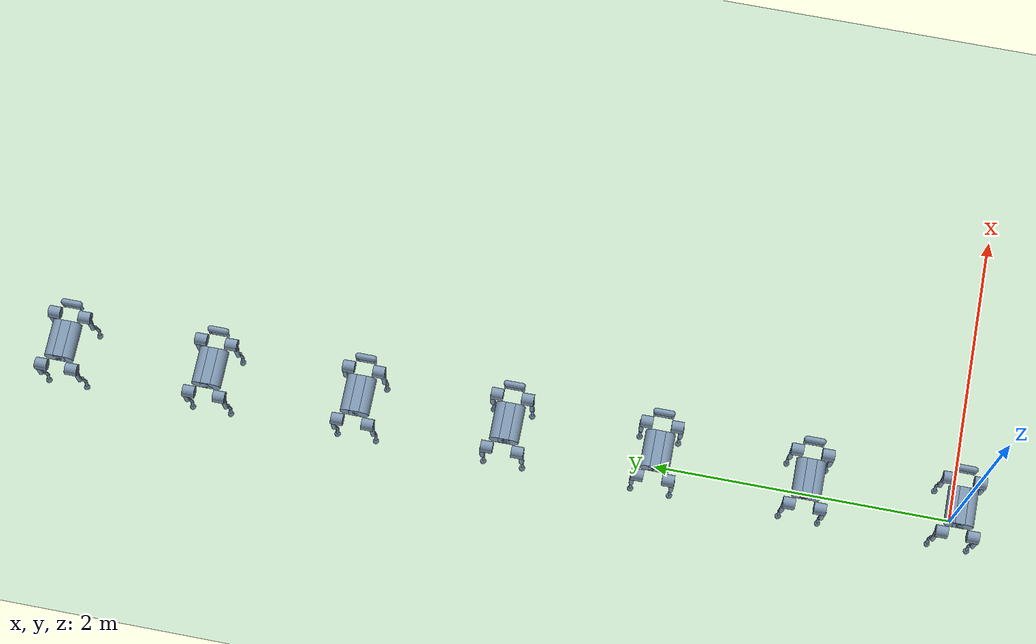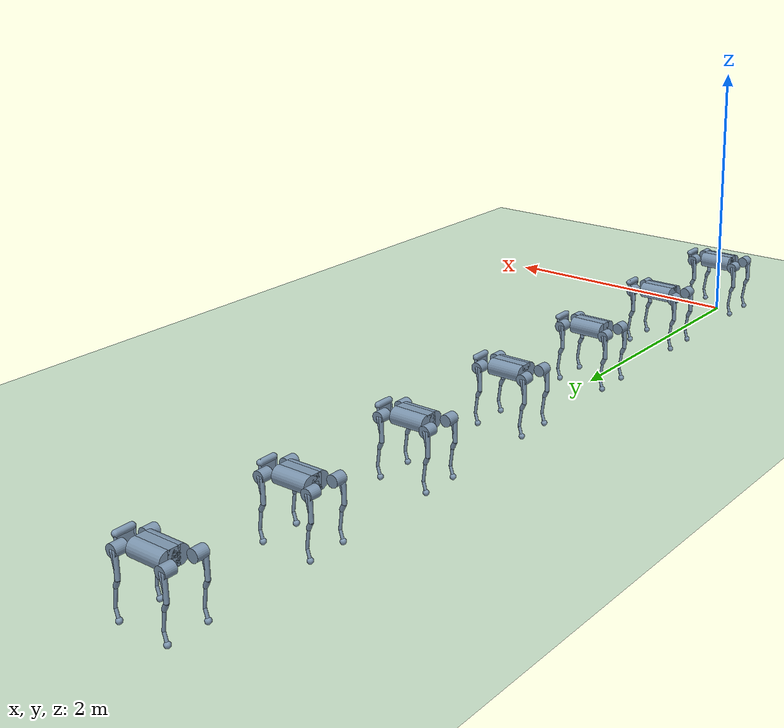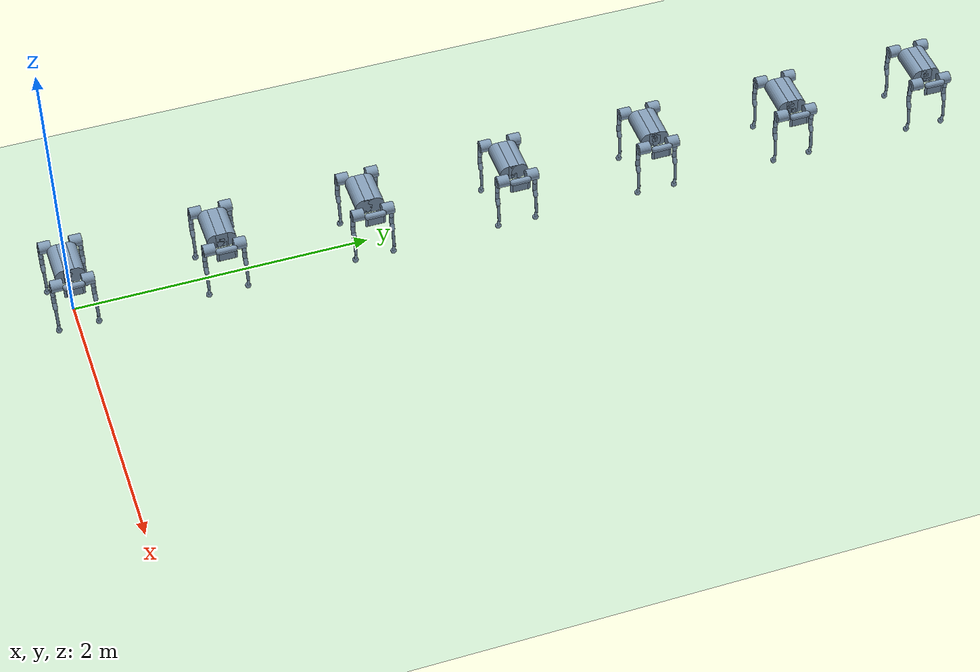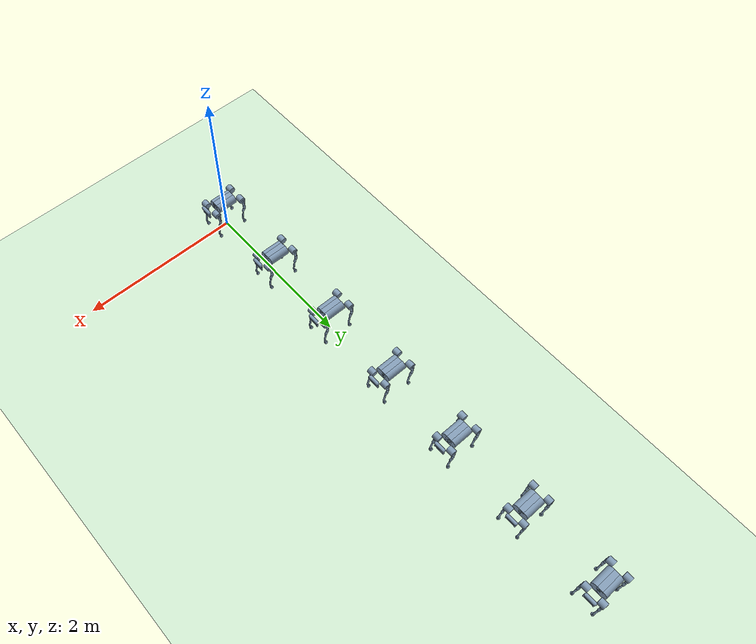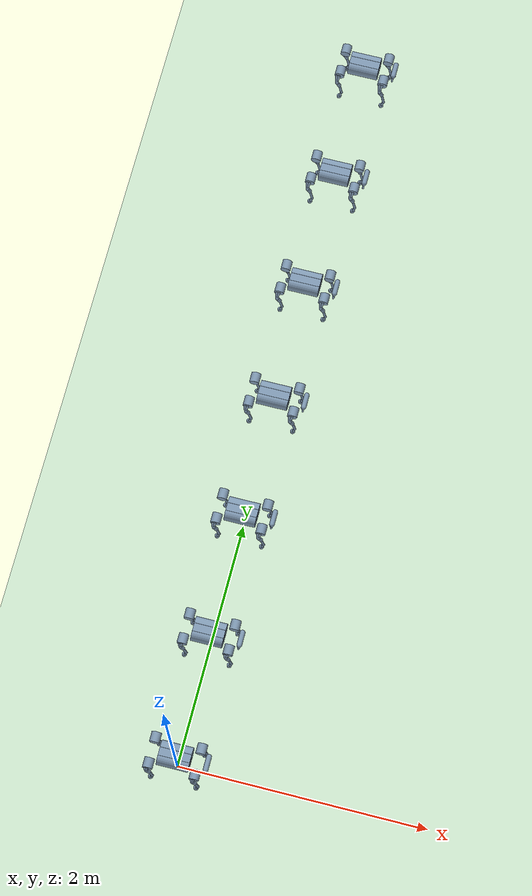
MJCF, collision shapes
<mujoco model="a1">
  <compiler angle="radian" meshdir="assets" texturedir="assets" autolimits="true"/>

  <option cone="elliptic" impratio="100" timestep="0.001"/> <!-- timestep from loco-mujoo-->

  <default>
    <motor ctrllimited="true" ctrlrange="-1.0 1.0"/>
    <default class="a1">
      <geom friction="0.6" margin="0.001"/>
      <joint axis="0 1 0" damping="2" armature="0.01" frictionloss="0.2"/>
      <motor ctrlrange="-33.5 33.5" ctrllimited="true"/>
      <default class="abduction">
        <joint axis="1 0 0" range="-0.802851 0.802851" damping="1"/>
        <position ctrlrange="-0.802851 0.802851"/>
      </default>
      <default class="hip">
        <joint range="-1.0472 4.18879"/>
        <position ctrlrange="-1.0472 4.18879"/>
      </default>
      <default class="knee">
        <joint range="-2.69653 -0.916298"/>
        <position ctrlrange="-2.69653 -0.916298"/>
      </default>
      <default class="visual">
        <geom type="mesh" contype="0" conaffinity="0" group="0" material="dark"/>
      </default>
      <default class="collision">
        <geom group="1" type="capsule" rgba="0.5 0.6 0.7 0.2"/>
        <default class="hip_left">
          <geom size="0.04 0.04" quat="1 1 0 0" type="cylinder" pos="0 0.055 0"/>
        </default>
        <default class="hip_right">
          <geom size="0.04 0.04" quat="1 1 0 0" type="cylinder" pos="0 -0.055 0"/>
        </default>
        <default class="thigh1">
          <geom size="0.015" fromto="-0.02 0 0 -0.02 0 -0.16"/>
        </default>
        <default class="thigh2">
          <geom size="0.015" fromto="0 0 0 -0.02 0 -0.1"/>
        </default>
        <default class="thigh3">
          <geom size="0.015" fromto="-0.02 0 -0.16 0 0 -0.2"/>
        </default>
        <default class="calf1">
          <geom size="0.01" fromto="0 0 0 0.02 0 -0.13"/>
        </default>
        <default class="calf2">
          <geom size="0.01" fromto="0.02 0 -0.13 0 0 -0.2"/>
        </default>
        <default class="foot">
          <geom type="sphere" size="0.02" pos="0 0 -0.2" priority="1" solimp="0.015 1 0.031"
              condim="6" friction="0.8 0.02 0.01"/>
        </default>
      </default>
    </default>
  </default>

  <asset>
    <texture builtin="gradient" height="100" rgb1=".4 .5 .6" rgb2="0 0 0" type="skybox" width="100"/>
    <texture name="texplane" type="2d" builtin="checker" rgb1=".2 .3 .4" rgb2=".1 0.15 0.2" width="100" height="100"></texture>
    <material name="MatPlane" reflectance="0.5" texture="texplane" texrepeat="1 1" texuniform="true"></material>
    <material name="dark" specular="0" shininess="0.25" rgba="0.2 0.2 0.2 1"/>
    <texture type="2d" name="trunk_A1" file="trunk_A1.png"/>
    <material name="carbonfibre" texture="trunk_A1" specular="0" shininess="0.25"/>

    <mesh class="a1" file="calf.obj"/>
    <mesh class="a1" file="hip.obj"/>
    <mesh class="a1" file="thigh.obj"/>
    <mesh class="a1" file="thigh_mirror.obj"/>
    <mesh class="a1" file="trunk.obj"/>
  </asset>

  <worldbody>
    <geom name="floor" pos="0 0 0" size="500 500 0.125" type="plane" material="MatPlane" condim="3" group="2" rgba="0.8 0.9 0.8 1"></geom>
    <light cutoff="100" diffuse="1 1 1" dir="-0 0 -1.3" directional="true" exponent="1" pos="0 0 1.3" specular=".1 .1 .1" castshadow="false"/>

    <body name="trunk___1" pos="0 0 0.43" childclass="a1">
      <light name="spotlight___1" mode="trackcom" pos="0 -0.25 2"/>
      <camera name="track___1" mode="trackcom" pos="0 -3 1" xyaxes="1 0 0 0 0.3 1"/>
      <joint name="trunk_tx___1" type="slide" pos="0 0 0" axis="       1        0        0" limited="false" range="-500        500" ref="0" armature="0" damping="0" stiffness="0"></joint>
      <joint name="trunk_ty___1" type="slide" pos="0 0 0" axis="       0        1        0" limited="false" range="-500        500" ref="0" armature="0" damping="0" stiffness="0"></joint>
      <joint name="trunk_tz___1" type="slide" pos="0 0 0" axis="       0        0        1" limited="false" range="-500        500" ref="0" armature="0" damping="0" stiffness="0"></joint>
      <joint name="trunk_list___1" type="hinge" pos="0 0 0" axis="       1        0        0" limited="false" range=" -3.141592654   3.141592654" ref="0" armature="0" damping="0" stiffness="0"></joint>
      <joint name="trunk_tilt___1" type="hinge" pos="0 0 0" axis="       0        1        0" limited="false" range=" -3.141592654   3.141592654" ref="0" armature="0" damping="0" stiffness="0"></joint>
      <joint name="trunk_rotation___1" type="hinge" pos="0 0 0" axis="       0        0        1" limited="false" range=" -3.141592654   3.141592654" ref="0" armature="0" damping="0" stiffness="0"></joint>

      <inertial mass="4.713" pos="0 0.0041 -0.0005"
          fullinertia="0.0158533 0.0377999 0.0456542 -3.66e-05 -6.11e-05 -2.75e-05"/>

      <geom class="visual" mesh="trunk" material="carbonfibre"/>
      <geom class="collision" size="0.125 0.04 0.057" type="box"/>
      <geom class="collision" quat="1 0 1 0" pos="0 -0.04 0" size="0.058 0.125" type="cylinder"/>
      <geom class="collision" quat="1 0 1 0" pos="0 +0.04 0" size="0.058 0.125" type="cylinder"/>
      <geom class="collision" pos="0.25 0 0" size="0.005 0.06 0.05" type="box"/>
      <geom class="collision" pos="0.25 0.06 -0.01" size="0.009 0.035"/>
      <geom class="collision" pos="0.25 -0.06 -0.01" size="0.009 0.035"/>
      <geom class="collision" pos="0.25 0 -0.05" size="0.005 0.06" quat="1 1 0 0"/>
      <geom class="collision" pos="0.255 0 0.0355" size="0.021 0.052" quat="1 1 0 0"/>
      <body name="FR_hip___1" pos="0.183 -0.047 0">
        <inertial mass="0.696" pos="-0.003311 -0.000635 3.1e-05"
            quat="0.507528 0.506268 0.491507 0.494499"
            diaginertia="0.000807752 0.00055293 0.000468983"/>
        <joint class="abduction" name="FR_hip_joint___1"/>
        <geom class="visual" mesh="hip" quat="0 1 0 0"/>
        <geom class="hip_right"/>
        <body name="FR_thigh___1" pos="0 -0.08505 0">
          <inertial mass="1.013" pos="-0.003237 0.022327 -0.027326"
              quat="0.999125 -0.00256393 -0.0409531 -0.00806091"
              diaginertia="0.00555739 0.00513936 0.00133944"/>
          <joint class="hip" name="FR_thigh_joint___1"/>
          <geom class="visual" mesh="thigh_mirror"/>
          <geom class="thigh1"/>
          <geom class="thigh2"/>
          <geom class="thigh3"/>
          <body name="FR_calf___1" pos="0 0 -0.2">
            <inertial mass="0.226" pos="0.00472659 0 -0.131975"
                quat="0.706886 0.017653 0.017653 0.706886"
                diaginertia="0.00340344 0.00339393 3.54834e-05"/>
            <joint class="knee" name="FR_calf_joint___1"/>
            <geom class="visual" mesh="calf"/>
            <geom class="calf1"/>
            <geom class="calf2"/>
            <geom class="foot" name="FR_foot___1"/>
          </body>
        </body>
      </body>
      <body name="FL_hip___1" pos="0.183 0.047 0">
        <inertial mass="0.696" pos="-0.003311 0.000635 3.1e-05"
            quat="0.494499 0.491507 0.506268 0.507528"
            diaginertia="0.000807752 0.00055293 0.000468983"/>
        <joint class="abduction" name="FL_hip_joint___1"/>
        <geom class="visual" mesh="hip"/>
        <geom class="hip_left"/>
        <geom class="collision" size="0.04 0.04" pos="0 0.055 0" quat="1 1 0 0" type="cylinder"/>
        <body name="FL_thigh___1" pos="0 0.08505 0">
          <inertial mass="1.013" pos="-0.003237 -0.022327 -0.027326"
              quat="0.999125 0.00256393 -0.0409531 0.00806091"
              diaginertia="0.00555739 0.00513936 0.00133944"/>
          <joint class="hip" name="FL_thigh_joint___1"/>
          <geom class="visual" mesh="thigh"/>
          <geom class="thigh1"/>
          <geom class="thigh2"/>
          <geom class="thigh3"/>
          <body name="FL_calf___1" pos="0 0 -0.2">
            <inertial mass="0.226" pos="0.00472659 0 -0.131975"
                quat="0.706886 0.017653 0.017653 0.706886"
                diaginertia="0.00340344 0.00339393 3.54834e-05"/>
            <joint class="knee" name="FL_calf_joint___1"/>
            <geom class="visual" mesh="calf"/>
            <geom class="calf1"/>
            <geom class="calf2"/>
            <geom class="foot"  name="FL_foot___1"/>
          </body>
        </body>
      </body>
      <body name="RR_hip___1" pos="-0.183 -0.047 0">
        <inertial mass="0.696" pos="0.003311 -0.000635 3.1e-05"
            quat="0.491507 0.494499 0.507528 0.506268"
            diaginertia="0.000807752 0.00055293 0.000468983"/>
        <joint class="abduction" name="RR_hip_joint___1"/>
        <geom class="visual" quat="0 0 0 -1" mesh="hip"/>
        <geom class="hip_right"/>
        <body name="RR_thigh___1" pos="0 -0.08505 0">
          <inertial mass="1.013" pos="-0.003237 0.022327 -0.027326"
              quat="0.999125 -0.00256393 -0.0409531 -0.00806091"
              diaginertia="0.00555739 0.00513936 0.00133944"/>
          <joint class="hip" name="RR_thigh_joint___1"/>
          <geom class="visual" mesh="thigh_mirror"/>
          <geom class="thigh1"/>
          <geom class="thigh2"/>
          <geom class="thigh3"/>
          <body name="RR_calf___1" pos="0 0 -0.2">
            <inertial mass="0.226" pos="0.00472659 0 -0.131975"
                quat="0.706886 0.017653 0.017653 0.706886"
                diaginertia="0.00340344 0.00339393 3.54834e-05"/>
            <joint class="knee" name="RR_calf_joint___1"/>
            <geom class="visual" mesh="calf"/>
            <geom class="calf1"/>
            <geom class="calf2"/>
            <geom class="foot" name="RR_foot___1"/>
          </body>
        </body>
      </body>
      <body name="RL_hip___1" pos="-0.183 0.047 0">
        <inertial mass="0.696" pos="0.003311 0.000635 3.1e-05"
            quat="0.506268 0.507528 0.494499 0.491507"
            diaginertia="0.000807752 0.00055293 0.000468983"/>
        <joint class="abduction" name="RL_hip_joint___1"/>
        <geom class="visual" quat="0 0 1 0" mesh="hip"/>
        <geom class="hip_left"/>
        <body name="RL_thigh___1" pos="0 0.08505 0">
          <inertial mass="1.013" pos="-0.003237 -0.022327 -0.027326"
              quat="0.999125 0.00256393 -0.0409531 0.00806091"
              diaginertia="0.00555739 0.00513936 0.00133944"/>
          <joint class="hip" name="RL_thigh_joint___1"/>
          <geom class="visual" mesh="thigh"/>
          <geom class="thigh1"/>
          <geom class="thigh2"/>
          <geom class="thigh3"/>
          <body name="RL_calf___1" pos="0 0 -0.2">
            <inertial mass="0.226" pos="0.00472659 0 -0.131975"
                quat="0.706886 0.017653 0.017653 0.706886"
                diaginertia="0.00340344 0.00339393 3.54834e-05"/>
            <joint class="knee" name="RL_calf_joint___1"/>
            <geom class="visual" mesh="calf"/>
            <geom class="calf1"/>
            <geom class="calf2"/>
            <geom class="foot" name="RL_foot___1"/>
          </body>
        </body>
      </body>
    </body>

    <body name="trunk___2" pos="0 1 0.43" childclass="a1">
      <light name="spotlight___2" mode="trackcom" pos="0 -0.25 2"/>
      <joint name="trunk_tx___2" type="slide" pos="0 0 0" axis="       1        0        0" limited="false" range="-500        500" ref="0" armature="0" damping="0" stiffness="0"></joint>
      <joint name="trunk_ty___2" type="slide" pos="0 0 0" axis="       0        1        0" limited="false" range="-500        500" ref="0" armature="0" damping="0" stiffness="0"></joint>
      <joint name="trunk_tz___2" type="slide" pos="0 0 0" axis="       0        0        1" limited="false" range="-500        500" ref="0" armature="0" damping="0" stiffness="0"></joint>
      <joint name="trunk_list___2" type="hinge" pos="0 0 0" axis="       1        0        0" limited="false" range=" -3.141592654   3.141592654" ref="0" armature="0" damping="0" stiffness="0"></joint>
      <joint name="trunk_tilt___2" type="hinge" pos="0 0 0" axis="       0        1        0" limited="false" range=" -3.141592654   3.141592654" ref="0" armature="0" damping="0" stiffness="0"></joint>
      <joint name="trunk_rotation___2" type="hinge" pos="0 0 0" axis="       0        0        1" limited="false" range=" -3.141592654   3.141592654" ref="0" armature="0" damping="0" stiffness="0"></joint>

      <inertial mass="4.713" pos="0 0.0041 -0.0005"
          fullinertia="0.0158533 0.0377999 0.0456542 -3.66e-05 -6.11e-05 -2.75e-05"/>

      <geom class="visual" mesh="trunk" material="carbonfibre"/>
      <geom class="collision" size="0.125 0.04 0.057" type="box"/>
      <geom class="collision" quat="1 0 1 0" pos="0 -0.04 0" size="0.058 0.125" type="cylinder"/>
      <geom class="collision" quat="1 0 1 0" pos="0 +0.04 0" size="0.058 0.125" type="cylinder"/>
      <geom class="collision" pos="0.25 0 0" size="0.005 0.06 0.05" type="box"/>
      <geom class="collision" pos="0.25 0.06 -0.01" size="0.009 0.035"/>
      <geom class="collision" pos="0.25 -0.06 -0.01" size="0.009 0.035"/>
      <geom class="collision" pos="0.25 0 -0.05" size="0.005 0.06" quat="1 1 0 0"/>
      <geom class="collision" pos="0.255 0 0.0355" size="0.021 0.052" quat="1 1 0 0"/>
      <body name="FR_hip___2" pos="0.183 -0.047 0">
        <inertial mass="0.696" pos="-0.003311 -0.000635 3.1e-05"
            quat="0.507528 0.506268 0.491507 0.494499"
            diaginertia="0.000807752 0.00055293 0.000468983"/>
        <joint class="abduction" name="FR_hip_joint___2"/>
        <geom class="visual" mesh="hip" quat="0 1 0 0"/>
        <geom class="hip_right"/>
        <body name="FR_thigh___2" pos="0 -0.08505 0">
          <inertial mass="1.013" pos="-0.003237 0.022327 -0.027326"
              quat="0.999125 -0.00256393 -0.0409531 -0.00806091"
              diaginertia="0.00555739 0.00513936 0.00133944"/>
          <joint class="hip" name="FR_thigh_joint___2"/>
          <geom class="visual" mesh="thigh_mirror"/>
          <geom class="thigh1"/>
          <geom class="thigh2"/>
          <geom class="thigh3"/>
          <body name="FR_calf___2" pos="0 0 -0.2">
            <inertial mass="0.226" pos="0.00472659 0 -0.131975"
                quat="0.706886 0.017653 0.017653 0.706886"
                diaginertia="0.00340344 0.00339393 3.54834e-05"/>
            <joint class="knee" name="FR_calf_joint___2"/>
            <geom class="visual" mesh="calf"/>
            <geom class="calf1"/>
            <geom class="calf2"/>
            <geom class="foot" name="FR_foot___2"/>
          </body>
        </body>
      </body>
      <body name="FL_hip___2" pos="0.183 0.047 0">
        <inertial mass="0.696" pos="-0.003311 0.000635 3.1e-05"
            quat="0.494499 0.491507 0.506268 0.507528"
            diaginertia="0.000807752 0.00055293 0.000468983"/>
        <joint class="abduction" name="FL_hip_joint___2"/>
        <geom class="visual" mesh="hip"/>
        <geom class="hip_left"/>
        <geom class="collision" size="0.04 0.04" pos="0 0.055 0" quat="1 1 0 0" type="cylinder"/>
        <body name="FL_thigh___2" pos="0 0.08505 0">
          <inertial mass="1.013" pos="-0.003237 -0.022327 -0.027326"
              quat="0.999125 0.00256393 -0.0409531 0.00806091"
              diaginertia="0.00555739 0.00513936 0.00133944"/>
          <joint class="hip" name="FL_thigh_joint___2"/>
          <geom class="visual" mesh="thigh"/>
          <geom class="thigh1"/>
          <geom class="thigh2"/>
          <geom class="thigh3"/>
          <body name="FL_calf___2" pos="0 0 -0.2">
            <inertial mass="0.226" pos="0.00472659 0 -0.131975"
                quat="0.706886 0.017653 0.017653 0.706886"
                diaginertia="0.00340344 0.00339393 3.54834e-05"/>
            <joint class="knee" name="FL_calf_joint___2"/>
            <geom class="visual" mesh="calf"/>
            <geom class="calf1"/>
            <geom class="calf2"/>
            <geom class="foot"  name="FL_foot___2"/>
          </body>
        </body>
      </body>
      <body name="RR_hip___2" pos="-0.183 -0.047 0">
        <inertial mass="0.696" pos="0.003311 -0.000635 3.1e-05"
            quat="0.491507 0.494499 0.507528 0.506268"
            diaginertia="0.000807752 0.00055293 0.000468983"/>
        <joint class="abduction" name="RR_hip_joint___2"/>
        <geom class="visual" quat="0 0 0 -1" mesh="hip"/>
        <geom class="hip_right"/>
        <body name="RR_thigh___2" pos="0 -0.08505 0">
          <inertial mass="1.013" pos="-0.003237 0.022327 -0.027326"
              quat="0.999125 -0.00256393 -0.0409531 -0.00806091"
              diaginertia="0.00555739 0.00513936 0.00133944"/>
          <joint class="hip" name="RR_thigh_joint___2"/>
          <geom class="visual" mesh="thigh_mirror"/>
          <geom class="thigh1"/>
          <geom class="thigh2"/>
          <geom class="thigh3"/>
          <body name="RR_calf___2" pos="0 0 -0.2">
            <inertial mass="0.226" pos="0.00472659 0 -0.131975"
                quat="0.706886 0.017653 0.017653 0.706886"
                diaginertia="0.00340344 0.00339393 3.54834e-05"/>
            <joint class="knee" name="RR_calf_joint___2"/>
            <geom class="visual" mesh="calf"/>
            <geom class="calf1"/>
            <geom class="calf2"/>
            <geom class="foot" name="RR_foot___2"/>
          </body>
        </body>
      </body>
      <body name="RL_hip___2" pos="-0.183 0.047 0">
        <inertial mass="0.696" pos="0.003311 0.000635 3.1e-05"
            quat="0.506268 0.507528 0.494499 0.491507"
            diaginertia="0.000807752 0.00055293 0.000468983"/>
        <joint class="abduction" name="RL_hip_joint___2"/>
        <geom class="visual" quat="0 0 1 0" mesh="hip"/>
        <geom class="hip_left"/>
        <body name="RL_thigh___2" pos="0 0.08505 0">
          <inertial mass="1.013" pos="-0.003237 -0.022327 -0.027326"
              quat="0.999125 0.00256393 -0.0409531 0.00806091"
              diaginertia="0.00555739 0.00513936 0.00133944"/>
          <joint class="hip" name="RL_thigh_joint___2"/>
          <geom class="visual" mesh="thigh"/>
          <geom class="thigh1"/>
          <geom class="thigh2"/>
          <geom class="thigh3"/>
          <body name="RL_calf___2" pos="0 0 -0.2">
            <inertial mass="0.226" pos="0.00472659 0 -0.131975"
                quat="0.706886 0.017653 0.017653 0.706886"
                diaginertia="0.00340344 0.00339393 3.54834e-05"/>
            <joint class="knee" name="RL_calf_joint___2"/>
            <geom class="visual" mesh="calf"/>
            <geom class="calf1"/>
            <geom class="calf2"/>
            <geom class="foot" name="RL_foot___2"/>
          </body>
        </body>
      </body>
    </body>

    <body name="trunk___3" pos="0 2 0.43" childclass="a1">
      <light name="spotlight___3" mode="trackcom" pos="0 -0.25 2"/>
      <joint name="trunk_tx___3" type="slide" pos="0 0 0" axis="       1        0        0" limited="false" range="-500        500" ref="0" armature="0" damping="0" stiffness="0"></joint>
      <joint name="trunk_ty___3" type="slide" pos="0 0 0" axis="       0        1        0" limited="false" range="-500        500" ref="0" armature="0" damping="0" stiffness="0"></joint>
      <joint name="trunk_tz___3" type="slide" pos="0 0 0" axis="       0        0        1" limited="false" range="-500        500" ref="0" armature="0" damping="0" stiffness="0"></joint>
      <joint name="trunk_list___3" type="hinge" pos="0 0 0" axis="       1        0        0" limited="false" range=" -3.141592654   3.141592654" ref="0" armature="0" damping="0" stiffness="0"></joint>
      <joint name="trunk_tilt___3" type="hinge" pos="0 0 0" axis="       0        1        0" limited="false" range=" -3.141592654   3.141592654" ref="0" armature="0" damping="0" stiffness="0"></joint>
      <joint name="trunk_rotation___3" type="hinge" pos="0 0 0" axis="       0        0        1" limited="false" range=" -3.141592654   3.141592654" ref="0" armature="0" damping="0" stiffness="0"></joint>

      <inertial mass="4.713" pos="0 0.0041 -0.0005"
          fullinertia="0.0158533 0.0377999 0.0456542 -3.66e-05 -6.11e-05 -2.75e-05"/>

      <geom class="visual" mesh="trunk" material="carbonfibre"/>
      <geom class="collision" size="0.125 0.04 0.057" type="box"/>
      <geom class="collision" quat="1 0 1 0" pos="0 -0.04 0" size="0.058 0.125" type="cylinder"/>
      <geom class="collision" quat="1 0 1 0" pos="0 +0.04 0" size="0.058 0.125" type="cylinder"/>
      <geom class="collision" pos="0.25 0 0" size="0.005 0.06 0.05" type="box"/>
      <geom class="collision" pos="0.25 0.06 -0.01" size="0.009 0.035"/>
      <geom class="collision" pos="0.25 -0.06 -0.01" size="0.009 0.035"/>
      <geom class="collision" pos="0.25 0 -0.05" size="0.005 0.06" quat="1 1 0 0"/>
      <geom class="collision" pos="0.255 0 0.0355" size="0.021 0.052" quat="1 1 0 0"/>
      <body name="FR_hip___3" pos="0.183 -0.047 0">
        <inertial mass="0.696" pos="-0.003311 -0.000635 3.1e-05"
            quat="0.507528 0.506268 0.491507 0.494499"
            diaginertia="0.000807752 0.00055293 0.000468983"/>
        <joint class="abduction" name="FR_hip_joint___3"/>
        <geom class="visual" mesh="hip" quat="0 1 0 0"/>
        <geom class="hip_right"/>
        <body name="FR_thigh___3" pos="0 -0.08505 0">
          <inertial mass="1.013" pos="-0.003237 0.022327 -0.027326"
              quat="0.999125 -0.00256393 -0.0409531 -0.00806091"
              diaginertia="0.00555739 0.00513936 0.00133944"/>
          <joint class="hip" name="FR_thigh_joint___3"/>
          <geom class="visual" mesh="thigh_mirror"/>
          <geom class="thigh1"/>
          <geom class="thigh2"/>
          <geom class="thigh3"/>
          <body name="FR_calf___3" pos="0 0 -0.2">
            <inertial mass="0.226" pos="0.00472659 0 -0.131975"
                quat="0.706886 0.017653 0.017653 0.706886"
                diaginertia="0.00340344 0.00339393 3.54834e-05"/>
            <joint class="knee" name="FR_calf_joint___3"/>
            <geom class="visual" mesh="calf"/>
            <geom class="calf1"/>
            <geom class="calf2"/>
            <geom class="foot" name="FR_foot___3"/>
          </body>
        </body>
      </body>
      <body name="FL_hip___3" pos="0.183 0.047 0">
        <inertial mass="0.696" pos="-0.003311 0.000635 3.1e-05"
            quat="0.494499 0.491507 0.506268 0.507528"
            diaginertia="0.000807752 0.00055293 0.000468983"/>
        <joint class="abduction" name="FL_hip_joint___3"/>
        <geom class="visual" mesh="hip"/>
        <geom class="hip_left"/>
        <geom class="collision" size="0.04 0.04" pos="0 0.055 0" quat="1 1 0 0" type="cylinder"/>
        <body name="FL_thigh___3" pos="0 0.08505 0">
          <inertial mass="1.013" pos="-0.003237 -0.022327 -0.027326"
              quat="0.999125 0.00256393 -0.0409531 0.00806091"
              diaginertia="0.00555739 0.00513936 0.00133944"/>
          <joint class="hip" name="FL_thigh_joint___3"/>
          <geom class="visual" mesh="thigh"/>
          <geom class="thigh1"/>
          <geom class="thigh2"/>
          <geom class="thigh3"/>
          <body name="FL_calf___3" pos="0 0 -0.2">
            <inertial mass="0.226" pos="0.00472659 0 -0.131975"
                quat="0.706886 0.017653 0.017653 0.706886"
                diaginertia="0.00340344 0.00339393 3.54834e-05"/>
            <joint class="knee" name="FL_calf_joint___3"/>
            <geom class="visual" mesh="calf"/>
            <geom class="calf1"/>
            <geom class="calf2"/>
            <geom class="foot"  name="FL_foot___3"/>
          </body>
        </body>
      </body>
      <body name="RR_hip___3" pos="-0.183 -0.047 0">
        <inertial mass="0.696" pos="0.003311 -0.000635 3.1e-05"
            quat="0.491507 0.494499 0.507528 0.506268"
            diaginertia="0.000807752 0.00055293 0.000468983"/>
        <joint class="abduction" name="RR_hip_joint___3"/>
        <geom class="visual" quat="0 0 0 -1" mesh="hip"/>
        <geom class="hip_right"/>
        <body name="RR_thigh___3" pos="0 -0.08505 0">
          <inertial mass="1.013" pos="-0.003237 0.022327 -0.027326"
              quat="0.999125 -0.00256393 -0.0409531 -0.00806091"
              diaginertia="0.00555739 0.00513936 0.00133944"/>
          <joint class="hip" name="RR_thigh_joint___3"/>
          <geom class="visual" mesh="thigh_mirror"/>
          <geom class="thigh1"/>
          <geom class="thigh2"/>
          <geom class="thigh3"/>
          <body name="RR_calf___3" pos="0 0 -0.2">
            <inertial mass="0.226" pos="0.00472659 0 -0.131975"
                quat="0.706886 0.017653 0.017653 0.706886"
                diaginertia="0.00340344 0.00339393 3.54834e-05"/>
            <joint class="knee" name="RR_calf_joint___3"/>
            <geom class="visual" mesh="calf"/>
            <geom class="calf1"/>
            <geom class="calf2"/>
            <geom class="foot" name="RR_foot___3"/>
          </body>
        </body>
      </body>
      <body name="RL_hip___3" pos="-0.183 0.047 0">
        <inertial mass="0.696" pos="0.003311 0.000635 3.1e-05"
            quat="0.506268 0.507528 0.494499 0.491507"
            diaginertia="0.000807752 0.00055293 0.000468983"/>
        <joint class="abduction" name="RL_hip_joint___3"/>
        <geom class="visual" quat="0 0 1 0" mesh="hip"/>
        <geom class="hip_left"/>
        <body name="RL_thigh___3" pos="0 0.08505 0">
          <inertial mass="1.013" pos="-0.003237 -0.022327 -0.027326"
              quat="0.999125 0.00256393 -0.0409531 0.00806091"
              diaginertia="0.00555739 0.00513936 0.00133944"/>
          <joint class="hip" name="RL_thigh_joint___3"/>
          <geom class="visual" mesh="thigh"/>
          <geom class="thigh1"/>
          <geom class="thigh2"/>
          <geom class="thigh3"/>
          <body name="RL_calf___3" pos="0 0 -0.2">
            <inertial mass="0.226" pos="0.00472659 0 -0.131975"
                quat="0.706886 0.017653 0.017653 0.706886"
                diaginertia="0.00340344 0.00339393 3.54834e-05"/>
            <joint class="knee" name="RL_calf_joint___3"/>
            <geom class="visual" mesh="calf"/>
            <geom class="calf1"/>
            <geom class="calf2"/>
            <geom class="foot" name="RL_foot___3"/>
          </body>
        </body>
      </body>
    </body>

    <body name="trunk___4" pos="0 3 0.43" childclass="a1">
      <light name="spotlight___4" mode="trackcom" pos="0 -0.25 2"/>
      <joint name="trunk_tx___4" type="slide" pos="0 0 0" axis="       1        0        0" limited="false" range="-500        500" ref="0" armature="0" damping="0" stiffness="0"></joint>
      <joint name="trunk_ty___4" type="slide" pos="0 0 0" axis="       0        1        0" limited="false" range="-500        500" ref="0" armature="0" damping="0" stiffness="0"></joint>
      <joint name="trunk_tz___4" type="slide" pos="0 0 0" axis="       0        0        1" limited="false" range="-500        500" ref="0" armature="0" damping="0" stiffness="0"></joint>
      <joint name="trunk_list___4" type="hinge" pos="0 0 0" axis="       1        0        0" limited="false" range=" -3.141592654   3.141592654" ref="0" armature="0" damping="0" stiffness="0"></joint>
      <joint name="trunk_tilt___4" type="hinge" pos="0 0 0" axis="       0        1        0" limited="false" range=" -3.141592654   3.141592654" ref="0" armature="0" damping="0" stiffness="0"></joint>
      <joint name="trunk_rotation___4" type="hinge" pos="0 0 0" axis="       0        0        1" limited="false" range=" -3.141592654   3.141592654" ref="0" armature="0" damping="0" stiffness="0"></joint>

      <inertial mass="4.713" pos="0 0.0041 -0.0005"
          fullinertia="0.0158533 0.0377999 0.0456542 -3.66e-05 -6.11e-05 -2.75e-05"/>

      <geom class="visual" mesh="trunk" material="carbonfibre"/>
      <geom class="collision" size="0.125 0.04 0.057" type="box"/>
      <geom class="collision" quat="1 0 1 0" pos="0 -0.04 0" size="0.058 0.125" type="cylinder"/>
      <geom class="collision" quat="1 0 1 0" pos="0 +0.04 0" size="0.058 0.125" type="cylinder"/>
      <geom class="collision" pos="0.25 0 0" size="0.005 0.06 0.05" type="box"/>
      <geom class="collision" pos="0.25 0.06 -0.01" size="0.009 0.035"/>
      <geom class="collision" pos="0.25 -0.06 -0.01" size="0.009 0.035"/>
      <geom class="collision" pos="0.25 0 -0.05" size="0.005 0.06" quat="1 1 0 0"/>
      <geom class="collision" pos="0.255 0 0.0355" size="0.021 0.052" quat="1 1 0 0"/>
      <body name="FR_hip___4" pos="0.183 -0.047 0">
        <inertial mass="0.696" pos="-0.003311 -0.000635 3.1e-05"
            quat="0.507528 0.506268 0.491507 0.494499"
            diaginertia="0.000807752 0.00055293 0.000468983"/>
        <joint class="abduction" name="FR_hip_joint___4"/>
        <geom class="visual" mesh="hip" quat="0 1 0 0"/>
        <geom class="hip_right"/>
        <body name="FR_thigh___4" pos="0 -0.08505 0">
          <inertial mass="1.013" pos="-0.003237 0.022327 -0.027326"
              quat="0.999125 -0.00256393 -0.0409531 -0.00806091"
              diaginertia="0.00555739 0.00513936 0.00133944"/>
          <joint class="hip" name="FR_thigh_joint___4"/>
          <geom class="visual" mesh="thigh_mirror"/>
          <geom class="thigh1"/>
          <geom class="thigh2"/>
          <geom class="thigh3"/>
          <body name="FR_calf___4" pos="0 0 -0.2">
            <inertial mass="0.226" pos="0.00472659 0 -0.131975"
                quat="0.706886 0.017653 0.017653 0.706886"
                diaginertia="0.00340344 0.00339393 3.54834e-05"/>
            <joint class="knee" name="FR_calf_joint___4"/>
            <geom class="visual" mesh="calf"/>
            <geom class="calf1"/>
            <geom class="calf2"/>
            <geom class="foot" name="FR_foot___4"/>
          </body>
        </body>
      </body>
      <body name="FL_hip___4" pos="0.183 0.047 0">
        <inertial mass="0.696" pos="-0.003311 0.000635 3.1e-05"
            quat="0.494499 0.491507 0.506268 0.507528"
            diaginertia="0.000807752 0.00055293 0.000468983"/>
        <joint class="abduction" name="FL_hip_joint___4"/>
        <geom class="visual" mesh="hip"/>
        <geom class="hip_left"/>
        <geom class="collision" size="0.04 0.04" pos="0 0.055 0" quat="1 1 0 0" type="cylinder"/>
        <body name="FL_thigh___4" pos="0 0.08505 0">
          <inertial mass="1.013" pos="-0.003237 -0.022327 -0.027326"
              quat="0.999125 0.00256393 -0.0409531 0.00806091"
              diaginertia="0.00555739 0.00513936 0.00133944"/>
          <joint class="hip" name="FL_thigh_joint___4"/>
          <geom class="visual" mesh="thigh"/>
          <geom class="thigh1"/>
          <geom class="thigh2"/>
          <geom class="thigh3"/>
          <body name="FL_calf___4" pos="0 0 -0.2">
            <inertial mass="0.226" pos="0.00472659 0 -0.131975"
                quat="0.706886 0.017653 0.017653 0.706886"
                diaginertia="0.00340344 0.00339393 3.54834e-05"/>
            <joint class="knee" name="FL_calf_joint___4"/>
            <geom class="visual" mesh="calf"/>
            <geom class="calf1"/>
            <geom class="calf2"/>
            <geom class="foot"  name="FL_foot___4"/>
          </body>
        </body>
      </body>
      <body name="RR_hip___4" pos="-0.183 -0.047 0">
        <inertial mass="0.696" pos="0.003311 -0.000635 3.1e-05"
            quat="0.491507 0.494499 0.507528 0.506268"
            diaginertia="0.000807752 0.00055293 0.000468983"/>
        <joint class="abduction" name="RR_hip_joint___4"/>
        <geom class="visual" quat="0 0 0 -1" mesh="hip"/>
        <geom class="hip_right"/>
        <body name="RR_thigh___4" pos="0 -0.08505 0">
          <inertial mass="1.013" pos="-0.003237 0.022327 -0.027326"
              quat="0.999125 -0.00256393 -0.0409531 -0.00806091"
              diaginertia="0.00555739 0.00513936 0.00133944"/>
          <joint class="hip" name="RR_thigh_joint___4"/>
          <geom class="visual" mesh="thigh_mirror"/>
          <geom class="thigh1"/>
          <geom class="thigh2"/>
          <geom class="thigh3"/>
          <body name="RR_calf___4" pos="0 0 -0.2">
            <inertial mass="0.226" pos="0.00472659 0 -0.131975"
                quat="0.706886 0.017653 0.017653 0.706886"
                diaginertia="0.00340344 0.00339393 3.54834e-05"/>
            <joint class="knee" name="RR_calf_joint___4"/>
            <geom class="visual" mesh="calf"/>
            <geom class="calf1"/>
            <geom class="calf2"/>
            <geom class="foot" name="RR_foot___4"/>
          </body>
        </body>
      </body>
      <body name="RL_hip___4" pos="-0.183 0.047 0">
        <inertial mass="0.696" pos="0.003311 0.000635 3.1e-05"
            quat="0.506268 0.507528 0.494499 0.491507"
            diaginertia="0.000807752 0.00055293 0.000468983"/>
        <joint class="abduction" name="RL_hip_joint___4"/>
        <geom class="visual" quat="0 0 1 0" mesh="hip"/>
        <geom class="hip_left"/>
        <body name="RL_thigh___4" pos="0 0.08505 0">
          <inertial mass="1.013" pos="-0.003237 -0.022327 -0.027326"
              quat="0.999125 0.00256393 -0.0409531 0.00806091"
              diaginertia="0.00555739 0.00513936 0.00133944"/>
          <joint class="hip" name="RL_thigh_joint___4"/>
          <geom class="visual" mesh="thigh"/>
          <geom class="thigh1"/>
          <geom class="thigh2"/>
          <geom class="thigh3"/>
          <body name="RL_calf___4" pos="0 0 -0.2">
            <inertial mass="0.226" pos="0.00472659 0 -0.131975"
                quat="0.706886 0.017653 0.017653 0.706886"
                diaginertia="0.00340344 0.00339393 3.54834e-05"/>
            <joint class="knee" name="RL_calf_joint___4"/>
            <geom class="visual" mesh="calf"/>
            <geom class="calf1"/>
            <geom class="calf2"/>
            <geom class="foot" name="RL_foot___4"/>
          </body>
        </body>
      </body>
    </body>

    <body name="trunk___5" pos="0 4 0.43" childclass="a1">
      <light name="spotlight___5" mode="trackcom" pos="0 -0.25 2"/>
      <joint name="trunk_tx___5" type="slide" pos="0 0 0" axis="       1        0        0" limited="false" range="-500        500" ref="0" armature="0" damping="0" stiffness="0"></joint>
      <joint name="trunk_ty___5" type="slide" pos="0 0 0" axis="       0        1        0" limited="false" range="-500        500" ref="0" armature="0" damping="0" stiffness="0"></joint>
      <joint name="trunk_tz___5" type="slide" pos="0 0 0" axis="       0        0        1" limited="false" range="-500        500" ref="0" armature="0" damping="0" stiffness="0"></joint>
      <joint name="trunk_list___5" type="hinge" pos="0 0 0" axis="       1        0        0" limited="false" range=" -3.141592654   3.141592654" ref="0" armature="0" damping="0" stiffness="0"></joint>
      <joint name="trunk_tilt___5" type="hinge" pos="0 0 0" axis="       0        1        0" limited="false" range=" -3.141592654   3.141592654" ref="0" armature="0" damping="0" stiffness="0"></joint>
      <joint name="trunk_rotation___5" type="hinge" pos="0 0 0" axis="       0        0        1" limited="false" range=" -3.141592654   3.141592654" ref="0" armature="0" damping="0" stiffness="0"></joint>

      <inertial mass="4.713" pos="0 0.0041 -0.0005"
          fullinertia="0.0158533 0.0377999 0.0456542 -3.66e-05 -6.11e-05 -2.75e-05"/>

      <geom class="visual" mesh="trunk" material="carbonfibre"/>
      <geom class="collision" size="0.125 0.04 0.057" type="box"/>
      <geom class="collision" quat="1 0 1 0" pos="0 -0.04 0" size="0.058 0.125" type="cylinder"/>
      <geom class="collision" quat="1 0 1 0" pos="0 +0.04 0" size="0.058 0.125" type="cylinder"/>
      <geom class="collision" pos="0.25 0 0" size="0.005 0.06 0.05" type="box"/>
      <geom class="collision" pos="0.25 0.06 -0.01" size="0.009 0.035"/>
      <geom class="collision" pos="0.25 -0.06 -0.01" size="0.009 0.035"/>
      <geom class="collision" pos="0.25 0 -0.05" size="0.005 0.06" quat="1 1 0 0"/>
      <geom class="collision" pos="0.255 0 0.0355" size="0.021 0.052" quat="1 1 0 0"/>
      <body name="FR_hip___5" pos="0.183 -0.047 0">
        <inertial mass="0.696" pos="-0.003311 -0.000635 3.1e-05"
            quat="0.507528 0.506268 0.491507 0.494499"
            diaginertia="0.000807752 0.00055293 0.000468983"/>
        <joint class="abduction" name="FR_hip_joint___5"/>
        <geom class="visual" mesh="hip" quat="0 1 0 0"/>
        <geom class="hip_right"/>
        <body name="FR_thigh___5" pos="0 -0.08505 0">
          <inertial mass="1.013" pos="-0.003237 0.022327 -0.027326"
              quat="0.999125 -0.00256393 -0.0409531 -0.00806091"
              diaginertia="0.00555739 0.00513936 0.00133944"/>
          <joint class="hip" name="FR_thigh_joint___5"/>
          <geom class="visual" mesh="thigh_mirror"/>
          <geom class="thigh1"/>
          <geom class="thigh2"/>
          <geom class="thigh3"/>
          <body name="FR_calf___5" pos="0 0 -0.2">
            <inertial mass="0.226" pos="0.00472659 0 -0.131975"
                quat="0.706886 0.017653 0.017653 0.706886"
                diaginertia="0.00340344 0.00339393 3.54834e-05"/>
            <joint class="knee" name="FR_calf_joint___5"/>
            <geom class="visual" mesh="calf"/>
            <geom class="calf1"/>
            <geom class="calf2"/>
            <geom class="foot" name="FR_foot___5"/>
          </body>
        </body>
      </body>
      <body name="FL_hip___5" pos="0.183 0.047 0">
        <inertial mass="0.696" pos="-0.003311 0.000635 3.1e-05"
            quat="0.494499 0.491507 0.506268 0.507528"
            diaginertia="0.000807752 0.00055293 0.000468983"/>
        <joint class="abduction" name="FL_hip_joint___5"/>
        <geom class="visual" mesh="hip"/>
        <geom class="hip_left"/>
        <geom class="collision" size="0.04 0.04" pos="0 0.055 0" quat="1 1 0 0" type="cylinder"/>
        <body name="FL_thigh___5" pos="0 0.08505 0">
          <inertial mass="1.013" pos="-0.003237 -0.022327 -0.027326"
              quat="0.999125 0.00256393 -0.0409531 0.00806091"
              diaginertia="0.00555739 0.00513936 0.00133944"/>
          <joint class="hip" name="FL_thigh_joint___5"/>
          <geom class="visual" mesh="thigh"/>
          <geom class="thigh1"/>
          <geom class="thigh2"/>
          <geom class="thigh3"/>
          <body name="FL_calf___5" pos="0 0 -0.2">
            <inertial mass="0.226" pos="0.00472659 0 -0.131975"
                quat="0.706886 0.017653 0.017653 0.706886"
                diaginertia="0.00340344 0.00339393 3.54834e-05"/>
            <joint class="knee" name="FL_calf_joint___5"/>
            <geom class="visual" mesh="calf"/>
            <geom class="calf1"/>
            <geom class="calf2"/>
            <geom class="foot"  name="FL_foot___5"/>
          </body>
        </body>
      </body>
      <body name="RR_hip___5" pos="-0.183 -0.047 0">
        <inertial mass="0.696" pos="0.003311 -0.000635 3.1e-05"
            quat="0.491507 0.494499 0.507528 0.506268"
            diaginertia="0.000807752 0.00055293 0.000468983"/>
        <joint class="abduction" name="RR_hip_joint___5"/>
        <geom class="visual" quat="0 0 0 -1" mesh="hip"/>
        <geom class="hip_right"/>
        <body name="RR_thigh___5" pos="0 -0.08505 0">
          <inertial mass="1.013" pos="-0.003237 0.022327 -0.027326"
              quat="0.999125 -0.00256393 -0.0409531 -0.00806091"
              diaginertia="0.00555739 0.00513936 0.00133944"/>
          <joint class="hip" name="RR_thigh_joint___5"/>
          <geom class="visual" mesh="thigh_mirror"/>
          <geom class="thigh1"/>
          <geom class="thigh2"/>
          <geom class="thigh3"/>
          <body name="RR_calf___5" pos="0 0 -0.2">
            <inertial mass="0.226" pos="0.00472659 0 -0.131975"
                quat="0.706886 0.017653 0.017653 0.706886"
                diaginertia="0.00340344 0.00339393 3.54834e-05"/>
            <joint class="knee" name="RR_calf_joint___5"/>
            <geom class="visual" mesh="calf"/>
            <geom class="calf1"/>
            <geom class="calf2"/>
            <geom class="foot" name="RR_foot___5"/>
          </body>
        </body>
      </body>
      <body name="RL_hip___5" pos="-0.183 0.047 0">
        <inertial mass="0.696" pos="0.003311 0.000635 3.1e-05"
            quat="0.506268 0.507528 0.494499 0.491507"
            diaginertia="0.000807752 0.00055293 0.000468983"/>
        <joint class="abduction" name="RL_hip_joint___5"/>
        <geom class="visual" quat="0 0 1 0" mesh="hip"/>
        <geom class="hip_left"/>
        <body name="RL_thigh___5" pos="0 0.08505 0">
          <inertial mass="1.013" pos="-0.003237 -0.022327 -0.027326"
              quat="0.999125 0.00256393 -0.0409531 0.00806091"
              diaginertia="0.00555739 0.00513936 0.00133944"/>
          <joint class="hip" name="RL_thigh_joint___5"/>
          <geom class="visual" mesh="thigh"/>
          <geom class="thigh1"/>
          <geom class="thigh2"/>
          <geom class="thigh3"/>
          <body name="RL_calf___5" pos="0 0 -0.2">
            <inertial mass="0.226" pos="0.00472659 0 -0.131975"
                quat="0.706886 0.017653 0.017653 0.706886"
                diaginertia="0.00340344 0.00339393 3.54834e-05"/>
            <joint class="knee" name="RL_calf_joint___5"/>
            <geom class="visual" mesh="calf"/>
            <geom class="calf1"/>
            <geom class="calf2"/>
            <geom class="foot" name="RL_foot___5"/>
          </body>
        </body>
      </body>
    </body>

    <body name="trunk___6" pos="0 5 0.43" childclass="a1">
      <light name="spotlight___6" mode="trackcom" pos="0 -0.25 2"/>
      <joint name="trunk_tx___6" type="slide" pos="0 0 0" axis="       1        0        0" limited="false" range="-500        500" ref="0" armature="0" damping="0" stiffness="0"></joint>
      <joint name="trunk_ty___6" type="slide" pos="0 0 0" axis="       0        1        0" limited="false" range="-500        500" ref="0" armature="0" damping="0" stiffness="0"></joint>
      <joint name="trunk_tz___6" type="slide" pos="0 0 0" axis="       0        0        1" limited="false" range="-500        500" ref="0" armature="0" damping="0" stiffness="0"></joint>
      <joint name="trunk_list___6" type="hinge" pos="0 0 0" axis="       1        0        0" limited="false" range=" -3.141592654   3.141592654" ref="0" armature="0" damping="0" stiffness="0"></joint>
      <joint name="trunk_tilt___6" type="hinge" pos="0 0 0" axis="       0        1        0" limited="false" range=" -3.141592654   3.141592654" ref="0" armature="0" damping="0" stiffness="0"></joint>
      <joint name="trunk_rotation___6" type="hinge" pos="0 0 0" axis="       0        0        1" limited="false" range=" -3.141592654   3.141592654" ref="0" armature="0" damping="0" stiffness="0"></joint>

      <inertial mass="4.713" pos="0 0.0041 -0.0005"
          fullinertia="0.0158533 0.0377999 0.0456542 -3.66e-05 -6.11e-05 -2.75e-05"/>

      <geom class="visual" mesh="trunk" material="carbonfibre"/>
      <geom class="collision" size="0.125 0.04 0.057" type="box"/>
      <geom class="collision" quat="1 0 1 0" pos="0 -0.04 0" size="0.058 0.125" type="cylinder"/>
      <geom class="collision" quat="1 0 1 0" pos="0 +0.04 0" size="0.058 0.125" type="cylinder"/>
      <geom class="collision" pos="0.25 0 0" size="0.005 0.06 0.05" type="box"/>
      <geom class="collision" pos="0.25 0.06 -0.01" size="0.009 0.035"/>
      <geom class="collision" pos="0.25 -0.06 -0.01" size="0.009 0.035"/>
      <geom class="collision" pos="0.25 0 -0.05" size="0.005 0.06" quat="1 1 0 0"/>
      <geom class="collision" pos="0.255 0 0.0355" size="0.021 0.052" quat="1 1 0 0"/>
      <body name="FR_hip___6" pos="0.183 -0.047 0">
        <inertial mass="0.696" pos="-0.003311 -0.000635 3.1e-05"
            quat="0.507528 0.506268 0.491507 0.494499"
            diaginertia="0.000807752 0.00055293 0.000468983"/>
        <joint class="abduction" name="FR_hip_joint___6"/>
        <geom class="visual" mesh="hip" quat="0 1 0 0"/>
        <geom class="hip_right"/>
        <body name="FR_thigh___6" pos="0 -0.08505 0">
          <inertial mass="1.013" pos="-0.003237 0.022327 -0.027326"
              quat="0.999125 -0.00256393 -0.0409531 -0.00806091"
              diaginertia="0.00555739 0.00513936 0.00133944"/>
          <joint class="hip" name="FR_thigh_joint___6"/>
          <geom class="visual" mesh="thigh_mirror"/>
          <geom class="thigh1"/>
          <geom class="thigh2"/>
          <geom class="thigh3"/>
          <body name="FR_calf___6" pos="0 0 -0.2">
            <inertial mass="0.226" pos="0.00472659 0 -0.131975"
                quat="0.706886 0.017653 0.017653 0.706886"
                diaginertia="0.00340344 0.00339393 3.54834e-05"/>
            <joint class="knee" name="FR_calf_joint___6"/>
            <geom class="visual" mesh="calf"/>
            <geom class="calf1"/>
            <geom class="calf2"/>
            <geom class="foot" name="FR_foot___6"/>
          </body>
        </body>
      </body>
      <body name="FL_hip___6" pos="0.183 0.047 0">
        <inertial mass="0.696" pos="-0.003311 0.000635 3.1e-05"
            quat="0.494499 0.491507 0.506268 0.507528"
            diaginertia="0.000807752 0.00055293 0.000468983"/>
        <joint class="abduction" name="FL_hip_joint___6"/>
        <geom class="visual" mesh="hip"/>
        <geom class="hip_left"/>
        <geom class="collision" size="0.04 0.04" pos="0 0.055 0" quat="1 1 0 0" type="cylinder"/>
        <body name="FL_thigh___6" pos="0 0.08505 0">
          <inertial mass="1.013" pos="-0.003237 -0.022327 -0.027326"
              quat="0.999125 0.00256393 -0.0409531 0.00806091"
              diaginertia="0.00555739 0.00513936 0.00133944"/>
          <joint class="hip" name="FL_thigh_joint___6"/>
          <geom class="visual" mesh="thigh"/>
          <geom class="thigh1"/>
          <geom class="thigh2"/>
          <geom class="thigh3"/>
          <body name="FL_calf___6" pos="0 0 -0.2">
            <inertial mass="0.226" pos="0.00472659 0 -0.131975"
                quat="0.706886 0.017653 0.017653 0.706886"
                diaginertia="0.00340344 0.00339393 3.54834e-05"/>
            <joint class="knee" name="FL_calf_joint___6"/>
            <geom class="visual" mesh="calf"/>
            <geom class="calf1"/>
            <geom class="calf2"/>
            <geom class="foot"  name="FL_foot___6"/>
          </body>
        </body>
      </body>
      <body name="RR_hip___6" pos="-0.183 -0.047 0">
        <inertial mass="0.696" pos="0.003311 -0.000635 3.1e-05"
            quat="0.491507 0.494499 0.507528 0.506268"
            diaginertia="0.000807752 0.00055293 0.000468983"/>
        <joint class="abduction" name="RR_hip_joint___6"/>
        <geom class="visual" quat="0 0 0 -1" mesh="hip"/>
        <geom class="hip_right"/>
        <body name="RR_thigh___6" pos="0 -0.08505 0">
          <inertial mass="1.013" pos="-0.003237 0.022327 -0.027326"
              quat="0.999125 -0.00256393 -0.0409531 -0.00806091"
              diaginertia="0.00555739 0.00513936 0.00133944"/>
          <joint class="hip" name="RR_thigh_joint___6"/>
          <geom class="visual" mesh="thigh_mirror"/>
          <geom class="thigh1"/>
          <geom class="thigh2"/>
          <geom class="thigh3"/>
          <body name="RR_calf___6" pos="0 0 -0.2">
            <inertial mass="0.226" pos="0.00472659 0 -0.131975"
                quat="0.706886 0.017653 0.017653 0.706886"
                diaginertia="0.00340344 0.00339393 3.54834e-05"/>
            <joint class="knee" name="RR_calf_joint___6"/>
            <geom class="visual" mesh="calf"/>
            <geom class="calf1"/>
            <geom class="calf2"/>
            <geom class="foot" name="RR_foot___6"/>
          </body>
        </body>
      </body>
      <body name="RL_hip___6" pos="-0.183 0.047 0">
        <inertial mass="0.696" pos="0.003311 0.000635 3.1e-05"
            quat="0.506268 0.507528 0.494499 0.491507"
            diaginertia="0.000807752 0.00055293 0.000468983"/>
        <joint class="abduction" name="RL_hip_joint___6"/>
        <geom class="visual" quat="0 0 1 0" mesh="hip"/>
        <geom class="hip_left"/>
        <body name="RL_thigh___6" pos="0 0.08505 0">
          <inertial mass="1.013" pos="-0.003237 -0.022327 -0.027326"
              quat="0.999125 0.00256393 -0.0409531 0.00806091"
              diaginertia="0.00555739 0.00513936 0.00133944"/>
          <joint class="hip" name="RL_thigh_joint___6"/>
          <geom class="visual" mesh="thigh"/>
          <geom class="thigh1"/>
          <geom class="thigh2"/>
          <geom class="thigh3"/>
          <body name="RL_calf___6" pos="0 0 -0.2">
            <inertial mass="0.226" pos="0.00472659 0 -0.131975"
                quat="0.706886 0.017653 0.017653 0.706886"
                diaginertia="0.00340344 0.00339393 3.54834e-05"/>
            <joint class="knee" name="RL_calf_joint___6"/>
            <geom class="visual" mesh="calf"/>
            <geom class="calf1"/>
            <geom class="calf2"/>
            <geom class="foot" name="RL_foot___6"/>
          </body>
        </body>
      </body>
    </body>

    <body name="trunk___7" pos="0 6 0.43" childclass="a1">
      <light name="spotlight___7" mode="trackcom" pos="0 -0.25 2"/>
      <joint name="trunk_tx___7" type="slide" pos="0 0 0" axis="       1        0        0" limited="false" range="-500        500" ref="0" armature="0" damping="0" stiffness="0"></joint>
      <joint name="trunk_ty___7" type="slide" pos="0 0 0" axis="       0        1        0" limited="false" range="-500        500" ref="0" armature="0" damping="0" stiffness="0"></joint>
      <joint name="trunk_tz___7" type="slide" pos="0 0 0" axis="       0        0        1" limited="false" range="-500        500" ref="0" armature="0" damping="0" stiffness="0"></joint>
      <joint name="trunk_list___7" type="hinge" pos="0 0 0" axis="       1        0        0" limited="false" range=" -3.141592654   3.141592654" ref="0" armature="0" damping="0" stiffness="0"></joint>
      <joint name="trunk_tilt___7" type="hinge" pos="0 0 0" axis="       0        1        0" limited="false" range=" -3.141592654   3.141592654" ref="0" armature="0" damping="0" stiffness="0"></joint>
      <joint name="trunk_rotation___7" type="hinge" pos="0 0 0" axis="       0        0        1" limited="false" range=" -3.141592654   3.141592654" ref="0" armature="0" damping="0" stiffness="0"></joint>

      <inertial mass="4.713" pos="0 0.0041 -0.0005"
          fullinertia="0.0158533 0.0377999 0.0456542 -3.66e-05 -6.11e-05 -2.75e-05"/>

      <geom class="visual" mesh="trunk" material="carbonfibre"/>
      <geom class="collision" size="0.125 0.04 0.057" type="box"/>
      <geom class="collision" quat="1 0 1 0" pos="0 -0.04 0" size="0.058 0.125" type="cylinder"/>
      <geom class="collision" quat="1 0 1 0" pos="0 +0.04 0" size="0.058 0.125" type="cylinder"/>
      <geom class="collision" pos="0.25 0 0" size="0.005 0.06 0.05" type="box"/>
      <geom class="collision" pos="0.25 0.06 -0.01" size="0.009 0.035"/>
      <geom class="collision" pos="0.25 -0.06 -0.01" size="0.009 0.035"/>
      <geom class="collision" pos="0.25 0 -0.05" size="0.005 0.06" quat="1 1 0 0"/>
      <geom class="collision" pos="0.255 0 0.0355" size="0.021 0.052" quat="1 1 0 0"/>
      <body name="FR_hip___7" pos="0.183 -0.047 0">
        <inertial mass="0.696" pos="-0.003311 -0.000635 3.1e-05"
            quat="0.507528 0.506268 0.491507 0.494499"
            diaginertia="0.000807752 0.00055293 0.000468983"/>
        <joint class="abduction" name="FR_hip_joint___7"/>
        <geom class="visual" mesh="hip" quat="0 1 0 0"/>
        <geom class="hip_right"/>
        <body name="FR_thigh___7" pos="0 -0.08505 0">
          <inertial mass="1.013" pos="-0.003237 0.022327 -0.027326"
              quat="0.999125 -0.00256393 -0.0409531 -0.00806091"
              diaginertia="0.00555739 0.00513936 0.00133944"/>
          <joint class="hip" name="FR_thigh_joint___7"/>
          <geom class="visual" mesh="thigh_mirror"/>
          <geom class="thigh1"/>
          <geom class="thigh2"/>
          <geom class="thigh3"/>
          <body name="FR_calf___7" pos="0 0 -0.2">
            <inertial mass="0.226" pos="0.00472659 0 -0.131975"
                quat="0.706886 0.017653 0.017653 0.706886"
                diaginertia="0.00340344 0.00339393 3.54834e-05"/>
            <joint class="knee" name="FR_calf_joint___7"/>
            <geom class="visual" mesh="calf"/>
            <geom class="calf1"/>
            <geom class="calf2"/>
            <geom class="foot" name="FR_foot___7"/>
          </body>
        </body>
      </body>
      <body name="FL_hip___7" pos="0.183 0.047 0">
        <inertial mass="0.696" pos="-0.003311 0.000635 3.1e-05"
            quat="0.494499 0.491507 0.506268 0.507528"
            diaginertia="0.000807752 0.00055293 0.000468983"/>
        <joint class="abduction" name="FL_hip_joint___7"/>
        <geom class="visual" mesh="hip"/>
        <geom class="hip_left"/>
        <geom class="collision" size="0.04 0.04" pos="0 0.055 0" quat="1 1 0 0" type="cylinder"/>
        <body name="FL_thigh___7" pos="0 0.08505 0">
          <inertial mass="1.013" pos="-0.003237 -0.022327 -0.027326"
              quat="0.999125 0.00256393 -0.0409531 0.00806091"
              diaginertia="0.00555739 0.00513936 0.00133944"/>
          <joint class="hip" name="FL_thigh_joint___7"/>
          <geom class="visual" mesh="thigh"/>
          <geom class="thigh1"/>
          <geom class="thigh2"/>
          <geom class="thigh3"/>
          <body name="FL_calf___7" pos="0 0 -0.2">
            <inertial mass="0.226" pos="0.00472659 0 -0.131975"
                quat="0.706886 0.017653 0.017653 0.706886"
                diaginertia="0.00340344 0.00339393 3.54834e-05"/>
            <joint class="knee" name="FL_calf_joint___7"/>
            <geom class="visual" mesh="calf"/>
            <geom class="calf1"/>
            <geom class="calf2"/>
            <geom class="foot"  name="FL_foot___7"/>
          </body>
        </body>
      </body>
      <body name="RR_hip___7" pos="-0.183 -0.047 0">
        <inertial mass="0.696" pos="0.003311 -0.000635 3.1e-05"
            quat="0.491507 0.494499 0.507528 0.506268"
            diaginertia="0.000807752 0.00055293 0.000468983"/>
        <joint class="abduction" name="RR_hip_joint___7"/>
        <geom class="visual" quat="0 0 0 -1" mesh="hip"/>
        <geom class="hip_right"/>
        <body name="RR_thigh___7" pos="0 -0.08505 0">
          <inertial mass="1.013" pos="-0.003237 0.022327 -0.027326"
              quat="0.999125 -0.00256393 -0.0409531 -0.00806091"
              diaginertia="0.00555739 0.00513936 0.00133944"/>
          <joint class="hip" name="RR_thigh_joint___7"/>
          <geom class="visual" mesh="thigh_mirror"/>
          <geom class="thigh1"/>
          <geom class="thigh2"/>
          <geom class="thigh3"/>
          <body name="RR_calf___7" pos="0 0 -0.2">
            <inertial mass="0.226" pos="0.00472659 0 -0.131975"
                quat="0.706886 0.017653 0.017653 0.706886"
                diaginertia="0.00340344 0.00339393 3.54834e-05"/>
            <joint class="knee" name="RR_calf_joint___7"/>
            <geom class="visual" mesh="calf"/>
            <geom class="calf1"/>
            <geom class="calf2"/>
            <geom class="foot" name="RR_foot___7"/>
          </body>
        </body>
      </body>
      <body name="RL_hip___7" pos="-0.183 0.047 0">
        <inertial mass="0.696" pos="0.003311 0.000635 3.1e-05"
            quat="0.506268 0.507528 0.494499 0.491507"
            diaginertia="0.000807752 0.00055293 0.000468983"/>
        <joint class="abduction" name="RL_hip_joint___7"/>
        <geom class="visual" quat="0 0 1 0" mesh="hip"/>
        <geom class="hip_left"/>
        <body name="RL_thigh___7" pos="0 0.08505 0">
          <inertial mass="1.013" pos="-0.003237 -0.022327 -0.027326"
              quat="0.999125 0.00256393 -0.0409531 0.00806091"
              diaginertia="0.00555739 0.00513936 0.00133944"/>
          <joint class="hip" name="RL_thigh_joint___7"/>
          <geom class="visual" mesh="thigh"/>
          <geom class="thigh1"/>
          <geom class="thigh2"/>
          <geom class="thigh3"/>
          <body name="RL_calf___7" pos="0 0 -0.2">
            <inertial mass="0.226" pos="0.00472659 0 -0.131975"
                quat="0.706886 0.017653 0.017653 0.706886"
                diaginertia="0.00340344 0.00339393 3.54834e-05"/>
            <joint class="knee" name="RL_calf_joint___7"/>
            <geom class="visual" mesh="calf"/>
            <geom class="calf1"/>
            <geom class="calf2"/>
            <geom class="foot" name="RL_foot___7"/>
          </body>
        </body>
      </body>
    </body>

  </worldbody>

  <actuator>
    <motor name="FR_hip___1" gear="34" joint="FR_hip_joint___1"></motor>
    <motor name="FR_thigh___1" gear="34" joint="FR_thigh_joint___1"></motor>
    <motor name="FR_calf___1" gear="34" joint="FR_calf_joint___1"></motor>
    <motor name="FL_hip___1" gear="34" joint="FL_hip_joint___1"></motor>
    <motor name="FL_thigh___1" gear="34" joint="FL_thigh_joint___1"></motor>
    <motor name="FL_calf___1" gear="34" joint="FL_calf_joint___1"></motor>
    <motor name="RR_hip___1" gear="34" joint="RR_hip_joint___1"></motor>
    <motor name="RR_thigh___1" gear="34" joint="RR_thigh_joint___1"></motor>
    <motor name="RR_calf___1" gear="34" joint="RR_calf_joint___1"></motor>
    <motor name="RL_hip___1" gear="34" joint="RL_hip_joint___1"></motor>
    <motor name="RL_thigh___1" gear="34" joint="RL_thigh_joint___1"></motor>
    <motor name="RL_calf___1" gear="34" joint="RL_calf_joint___1"></motor>
  </actuator>

  <actuator>
    <motor name="FR_hip___2" gear="34" joint="FR_hip_joint___2"></motor>
    <motor name="FR_thigh___2" gear="34" joint="FR_thigh_joint___2"></motor>
    <motor name="FR_calf___2" gear="34" joint="FR_calf_joint___2"></motor>
    <motor name="FL_hip___2" gear="34" joint="FL_hip_joint___2"></motor>
    <motor name="FL_thigh___2" gear="34" joint="FL_thigh_joint___2"></motor>
    <motor name="FL_calf___2" gear="34" joint="FL_calf_joint___2"></motor>
    <motor name="RR_hip___2" gear="34" joint="RR_hip_joint___2"></motor>
    <motor name="RR_thigh___2" gear="34" joint="RR_thigh_joint___2"></motor>
    <motor name="RR_calf___2" gear="34" joint="RR_calf_joint___2"></motor>
    <motor name="RL_hip___2" gear="34" joint="RL_hip_joint___2"></motor>
    <motor name="RL_thigh___2" gear="34" joint="RL_thigh_joint___2"></motor>
    <motor name="RL_calf___2" gear="34" joint="RL_calf_joint___2"></motor>
  </actuator>

  <actuator>
    <motor name="FR_hip___3" gear="34" joint="FR_hip_joint___3"></motor>
    <motor name="FR_thigh___3" gear="34" joint="FR_thigh_joint___3"></motor>
    <motor name="FR_calf___3" gear="34" joint="FR_calf_joint___3"></motor>
    <motor name="FL_hip___3" gear="34" joint="FL_hip_joint___3"></motor>
    <motor name="FL_thigh___3" gear="34" joint="FL_thigh_joint___3"></motor>
    <motor name="FL_calf___3" gear="34" joint="FL_calf_joint___3"></motor>
    <motor name="RR_hip___3" gear="34" joint="RR_hip_joint___3"></motor>
    <motor name="RR_thigh___3" gear="34" joint="RR_thigh_joint___3"></motor>
    <motor name="RR_calf___3" gear="34" joint="RR_calf_joint___3"></motor>
    <motor name="RL_hip___3" gear="34" joint="RL_hip_joint___3"></motor>
    <motor name="RL_thigh___3" gear="34" joint="RL_thigh_joint___3"></motor>
    <motor name="RL_calf___3" gear="34" joint="RL_calf_joint___3"></motor>
  </actuator>

  <actuator>
    <motor name="FR_hip___4" gear="34" joint="FR_hip_joint___4"></motor>
    <motor name="FR_thigh___4" gear="34" joint="FR_thigh_joint___4"></motor>
    <motor name="FR_calf___4" gear="34" joint="FR_calf_joint___4"></motor>
    <motor name="FL_hip___4" gear="34" joint="FL_hip_joint___4"></motor>
    <motor name="FL_thigh___4" gear="34" joint="FL_thigh_joint___4"></motor>
    <motor name="FL_calf___4" gear="34" joint="FL_calf_joint___4"></motor>
    <motor name="RR_hip___4" gear="34" joint="RR_hip_joint___4"></motor>
    <motor name="RR_thigh___4" gear="34" joint="RR_thigh_joint___4"></motor>
    <motor name="RR_calf___4" gear="34" joint="RR_calf_joint___4"></motor>
    <motor name="RL_hip___4" gear="34" joint="RL_hip_joint___4"></motor>
    <motor name="RL_thigh___4" gear="34" joint="RL_thigh_joint___4"></motor>
    <motor name="RL_calf___4" gear="34" joint="RL_calf_joint___4"></motor>
  </actuator>

  <actuator>
    <motor name="FR_hip___5" gear="34" joint="FR_hip_joint___5"></motor>
    <motor name="FR_thigh___5" gear="34" joint="FR_thigh_joint___5"></motor>
    <motor name="FR_calf___5" gear="34" joint="FR_calf_joint___5"></motor>
    <motor name="FL_hip___5" gear="34" joint="FL_hip_joint___5"></motor>
    <motor name="FL_thigh___5" gear="34" joint="FL_thigh_joint___5"></motor>
    <motor name="FL_calf___5" gear="34" joint="FL_calf_joint___5"></motor>
    <motor name="RR_hip___5" gear="34" joint="RR_hip_joint___5"></motor>
    <motor name="RR_thigh___5" gear="34" joint="RR_thigh_joint___5"></motor>
    <motor name="RR_calf___5" gear="34" joint="RR_calf_joint___5"></motor>
    <motor name="RL_hip___5" gear="34" joint="RL_hip_joint___5"></motor>
    <motor name="RL_thigh___5" gear="34" joint="RL_thigh_joint___5"></motor>
    <motor name="RL_calf___5" gear="34" joint="RL_calf_joint___5"></motor>
  </actuator>

    <actuator>
    <motor name="FR_hip___6" gear="34" joint="FR_hip_joint___6"></motor>
    <motor name="FR_thigh___6" gear="34" joint="FR_thigh_joint___6"></motor>
    <motor name="FR_calf___6" gear="34" joint="FR_calf_joint___6"></motor>
    <motor name="FL_hip___6" gear="34" joint="FL_hip_joint___6"></motor>
    <motor name="FL_thigh___6" gear="34" joint="FL_thigh_joint___6"></motor>
    <motor name="FL_calf___6" gear="34" joint="FL_calf_joint___6"></motor>
    <motor name="RR_hip___6" gear="34" joint="RR_hip_joint___6"></motor>
    <motor name="RR_thigh___6" gear="34" joint="RR_thigh_joint___6"></motor>
    <motor name="RR_calf___6" gear="34" joint="RR_calf_joint___6"></motor>
    <motor name="RL_hip___6" gear="34" joint="RL_hip_joint___6"></motor>
    <motor name="RL_thigh___6" gear="34" joint="RL_thigh_joint___6"></motor>
    <motor name="RL_calf___6" gear="34" joint="RL_calf_joint___6"></motor>
  </actuator>

  <actuator>
    <motor name="FR_hip___7" gear="34" joint="FR_hip_joint___7"></motor>
    <motor name="FR_thigh___7" gear="34" joint="FR_thigh_joint___7"></motor>
    <motor name="FR_calf___7" gear="34" joint="FR_calf_joint___7"></motor>
    <motor name="FL_hip___7" gear="34" joint="FL_hip_joint___7"></motor>
    <motor name="FL_thigh___7" gear="34" joint="FL_thigh_joint___7"></motor>
    <motor name="FL_calf___7" gear="34" joint="FL_calf_joint___7"></motor>
    <motor name="RR_hip___7" gear="34" joint="RR_hip_joint___7"></motor>
    <motor name="RR_thigh___7" gear="34" joint="RR_thigh_joint___7"></motor>
    <motor name="RR_calf___7" gear="34" joint="RR_calf_joint___7"></motor>
    <motor name="RL_hip___7" gear="34" joint="RL_hip_joint___7"></motor>
    <motor name="RL_thigh___7" gear="34" joint="RL_thigh_joint___7"></motor>
    <motor name="RL_calf___7" gear="34" joint="RL_calf_joint___7"></motor>
  </actuator>

</mujoco>
